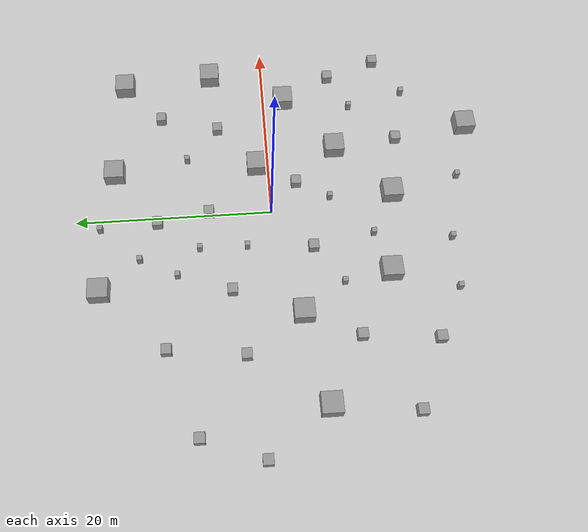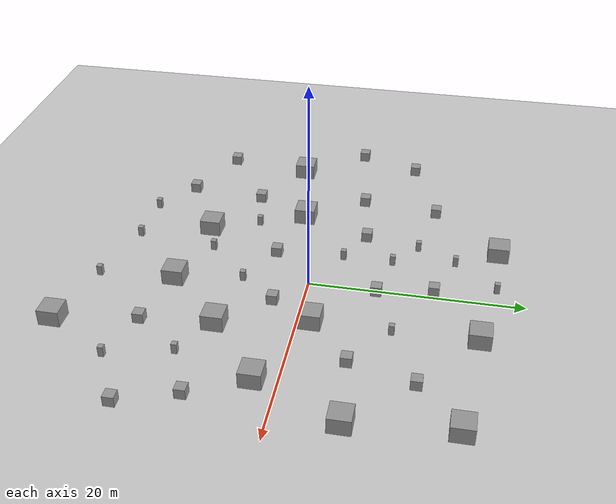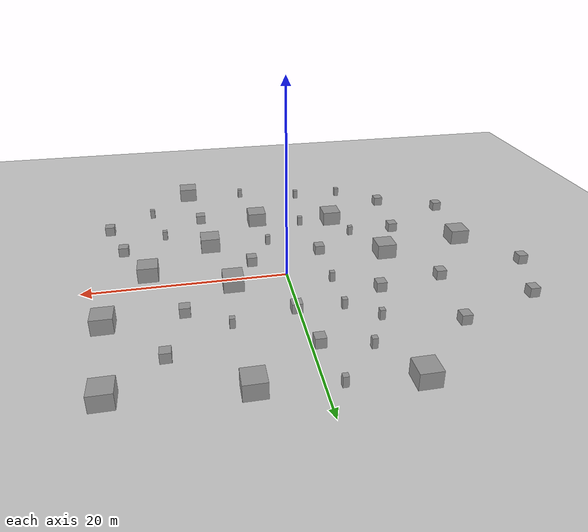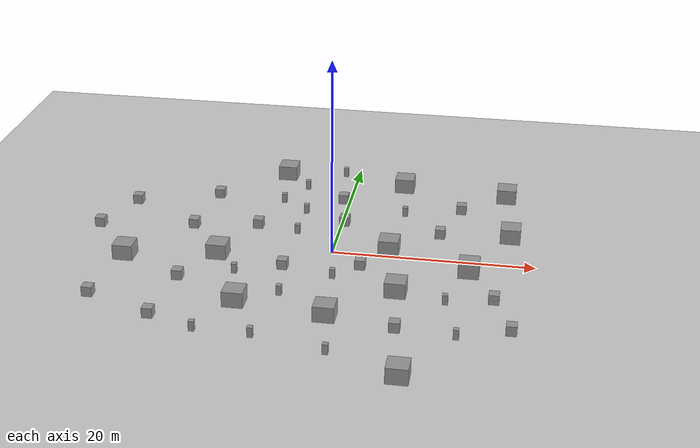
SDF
<sdf version="1.6">
 <world name="default">
  <light name="sun" type="directional">
   <pose>0 0 10 0 -0 0</pose>
   <diffuse>0.8 0.8 0.8 1</diffuse>
   <specular>0.2 0.2 0.2 1</specular>
   <attenuation>
    <range>1000</range>
    <constant>0.9</constant>
    <linear>0.01</linear>
    <quadratic>0.001</quadratic>
   </attenuation>
   <direction>-0.5 0.1 -0.9</direction>
  </light>
  <model name="ground_plane">
   <static>1</static>
   <link name="link">
    <collision name="collision">
     <geometry><plane><normal>0 0 1</normal><size>100 100</size></plane></geometry>
     <surface>
      <contact><collide_bitmask>65535</collide_bitmask></contact>
      <friction><ode><mu>100</mu><mu2>50</mu2></ode></friction>
     </surface>
    </collision>
    <visual name="visual">
     <cast_shadows>0</cast_shadows>
     <geometry><plane><normal>0 0 1</normal><size>100 100</size></plane></geometry>
     <material>
      <script><uri>file://media/materials/scripts/gazebo.material</uri><name>Gazebo/Grey</name></script>
     </material>
    </visual>
   </link>
  </model>
  <gravity>0 0 -9.8</gravity>
  <magnetic_field>6e-06 2.3e-05 -4.2e-05</magnetic_field>
  <atmosphere type="adiabatic"/>
  <physics name="default_physics" default="0" type="ode">
   <max_step_size>0.001</max_step_size>
   <real_time_factor>1</real_time_factor>
   <real_time_update_rate>1000</real_time_update_rate>
  </physics>
  <scene><ambient>0.4 0.4 0.4 1</ambient><background>0.7 0.7 0.7 1</background><shadows>1</shadows></scene>
  <audio><device>default</device></audio>
  <spherical_coordinates>
   <surface_model>EARTH_WGS84</surface_model>
   <latitude_deg>0</latitude_deg>
   <longitude_deg>0</longitude_deg>
   <elevation>0</elevation>
   <heading_deg>0</heading_deg>
  </spherical_coordinates>
  <model name="unit_box">
   <pose>-4.20212 -3.90314 0.5 0 -0 0</pose>
   <link name="link">
    <inertial>
     <mass>1</mass>
     <inertia>
      <ixx>0.166667</ixx>
      <ixy>0</ixy>
      <ixz>0</ixz>
      <iyy>0.166667</iyy>
      <iyz>0</iyz>
      <izz>0.166667</izz>
     </inertia>
    </inertial>
    <collision name="collision"><geometry><box><size>1 1 1</size></box></geometry></collision>
    <visual name="visual">
     <geometry><box><size>1 1 1</size></box></geometry>
     <material>
      <script><name>Gazebo/Grey</name><uri>file://media/materials/scripts/gazebo.material</uri></script>
     </material>
    </visual>
   </link>
  </model>
  <model name="unit_box_0">
   <pose>-8.36923 4.37364 0.5 -0 -0 -0</pose>
   <link name="link">
    <inertial>
     <mass>1</mass>
     <inertia>
      <ixx>0.166667</ixx>
      <ixy>0</ixy>
      <ixz>0</ixz>
      <iyy>0.166667</iyy>
      <iyz>0</iyz>
      <izz>0.166667</izz>
     </inertia>
    </inertial>
    <collision name="collision"><geometry><box><size>1 1 1</size></box></geometry></collision>
    <visual name="visual">
     <geometry><box><size>1 1 1</size></box></geometry>
     <material>
      <script><name>Gazebo/Grey</name><uri>file://media/materials/scripts/gazebo.material</uri></script>
     </material>
    </visual>
   </link>
  </model>
  <model name="unit_box_1">
   <pose>-0.684189 11.6081 0.5 0 -0 0</pose>
   <link name="link">
    <inertial>
     <mass>1</mass>
     <inertia>
      <ixx>0.166667</ixx>
      <ixy>0</ixy>
      <ixz>0</ixz>
      <iyy>0.166667</iyy>
      <iyz>0</iyz>
      <izz>0.166667</izz>
     </inertia>
    </inertial>
    <collision name="collision"><geometry><box><size>1 1 1</size></box></geometry></collision>
    <visual name="visual">
     <geometry><box><size>1 1 1</size></box></geometry>
     <material>
      <script><name>Gazebo/Grey</name><uri>file://media/materials/scripts/gazebo.material</uri></script>
     </material>
    </visual>
   </link>
  </model>
  <model name="0.5x0.5_cube_4">
   <link name="link">
    <inertial>
     <mass>1</mass>
     <inertia>
      <ixx>0.166667</ixx>
      <ixy>0</ixy>
      <ixz>0</ixz>
      <iyy>0.166667</iyy>
      <iyz>0</iyz>
      <izz>0.166667</izz>
     </inertia>
    </inertial>
    <visual name="visual">
     <geometry><box><size>0.5 0.5 1</size></box></geometry>
     <material>
      <script><name>Gazebo/Grey</name><uri>file://media/materials/scripts/gazebo.material</uri></script>
      <shader type="vertex"><normal_map>__default__</normal_map></shader>
      <ambient>0.3 0.3 0.3 1</ambient>
      <diffuse>0.7 0.7 0.7 1</diffuse>
      <specular>0.01 0.01 0.01 1</specular>
      <emissive>0 0 0 1</emissive>
     </material>
     <pose>0 0 0.5 0 -0 0</pose>
    </visual>
    <collision name="collision">
     <geometry><box><size>1 1 1</size></box></geometry>
     <surface>
      <friction>
       <ode><mu>1</mu><mu2>1</mu2><fdir1>0 0 0</fdir1><slip1>0</slip1><slip2>0</slip2></ode>
       <torsional>
        <coefficient>1</coefficient>
        <patch_radius>0</patch_radius>
        <surface_radius>0</surface_radius>
        <use_patch_radius>1</use_patch_radius>
        <ode><slip>0</slip></ode>
       </torsional>
      </friction>
      <bounce><restitution_coefficient>0</restitution_coefficient><threshold>1e+06</threshold></bounce>
      <contact>
       <collide_without_contact>0</collide_without_contact>
       <collide_without_contact_bitmask>1</collide_without_contact_bitmask>
       <collide_bitmask>1</collide_bitmask>
       <ode>
        <soft_cfm>0</soft_cfm>
        <soft_erp>0.2</soft_erp>
        <kp>1e+13</kp>
        <kd>1</kd>
        <max_vel>0.01</max_vel>
        <min_depth>0</min_depth>
       </ode>
       <bullet>
        <split_impulse>1</split_impulse>
        <split_impulse_penetration_threshold>-0.01</split_impulse_penetration_threshold>
        <soft_cfm>0</soft_cfm>
        <soft_erp>0.2</soft_erp>
        <kp>1e+13</kp>
        <kd>1</kd>
       </bullet>
      </contact>
     </surface>
    </collision>
   </link>
   <static>0</static>
   <pose>1.04625 -6.00454 0.5 0 -0 0</pose>
  </model>
  <model name="2x2_cube">
   <link name="link">
    <inertial>
     <mass>1</mass>
     <inertia>
      <ixx>0.166667</ixx>
      <ixy>0</ixy>
      <ixz>0</ixz>
      <iyy>0.166667</iyy>
      <iyz>0</iyz>
      <izz>0.166667</izz>
     </inertia>
    </inertial>
    <visual name="visual">
     <geometry><box><size>2 2 2</size></box></geometry>
     <material>
      <script><name>Gazebo/Grey</name><uri>file://media/materials/scripts/gazebo.material</uri></script>
      <shader type="vertex"><normal_map>__default__</normal_map></shader>
      <ambient>0.3 0.3 0.3 1</ambient>
      <diffuse>0.7 0.7 0.7 1</diffuse>
      <specular>0.01 0.01 0.01 1</specular>
      <emissive>0 0 0 1</emissive>
     </material>
    </visual>
    <collision name="collision">
     <geometry><box><size>1 1 1</size></box></geometry>
     <surface>
      <friction>
       <ode><mu>1</mu><mu2>1</mu2><fdir1>0 0 0</fdir1><slip1>0</slip1><slip2>0</slip2></ode>
       <torsional>
        <coefficient>1</coefficient>
        <patch_radius>0</patch_radius>
        <surface_radius>0</surface_radius>
        <use_patch_radius>1</use_patch_radius>
        <ode><slip>0</slip></ode>
       </torsional>
      </friction>
      <bounce><restitution_coefficient>0</restitution_coefficient><threshold>1e+06</threshold></bounce>
      <contact>
       <collide_without_contact>0</collide_without_contact>
       <collide_without_contact_bitmask>1</collide_without_contact_bitmask>
       <collide_bitmask>1</collide_bitmask>
       <ode>
        <soft_cfm>0</soft_cfm>
        <soft_erp>0.2</soft_erp>
        <kp>1e+13</kp>
        <kd>1</kd>
        <max_vel>0.01</max_vel>
        <min_depth>0</min_depth>
       </ode>
       <bullet>
        <split_impulse>1</split_impulse>
        <split_impulse_penetration_threshold>-0.01</split_impulse_penetration_threshold>
        <soft_cfm>0</soft_cfm>
        <soft_erp>0.2</soft_erp>
        <kp>1e+13</kp>
        <kd>1</kd>
       </bullet>
      </contact>
     </surface>
    </collision>
   </link>
   <static>0</static>
   <pose>5.52974 1.21304 0.5 0 -0 0</pose>
  </model>
  <model name="unit_box_2">
   <pose>0.255872 6.3816 0.5 -0 -0 -0</pose>
   <link name="link">
    <inertial>
     <mass>1</mass>
     <inertia>
      <ixx>0.166667</ixx>
      <ixy>0</ixy>
      <ixz>0</ixz>
      <iyy>0.166667</iyy>
      <iyz>0</iyz>
      <izz>0.166667</izz>
     </inertia>
    </inertial>
    <collision name="collision"><geometry><box><size>1 1 1</size></box></geometry></collision>
    <visual name="visual">
     <geometry><box><size>1 1 1</size></box></geometry>
     <material>
      <script><name>Gazebo/Grey</name><uri>file://media/materials/scripts/gazebo.material</uri></script>
     </material>
    </visual>
   </link>
  </model>
  <model name="0.5x0.5_cube_4_0">
   <link name="link">
    <inertial>
     <mass>1</mass>
     <inertia>
      <ixx>0.166667</ixx>
      <ixy>0</ixy>
      <ixz>0</ixz>
      <iyy>0.166667</iyy>
      <iyz>0</iyz>
      <izz>0.166667</izz>
     </inertia>
    </inertial>
    <visual name="visual">
     <geometry><box><size>0.5 0.5 1</size></box></geometry>
     <material>
      <script><name>Gazebo/Grey</name><uri>file://media/materials/scripts/gazebo.material</uri></script>
      <shader type="vertex"><normal_map>__default__</normal_map></shader>
      <ambient>0.3 0.3 0.3 1</ambient>
      <diffuse>0.7 0.7 0.7 1</diffuse>
      <specular>0.01 0.01 0.01 1</specular>
      <emissive>0 0 0 1</emissive>
     </material>
     <pose>0 0 0.5 0 -0 0</pose>
    </visual>
    <collision name="collision">
     <geometry><box><size>1 1 1</size></box></geometry>
     <surface>
      <friction>
       <ode><mu>1</mu><mu2>1</mu2><fdir1>0 0 0</fdir1><slip1>0</slip1><slip2>0</slip2></ode>
       <torsional>
        <coefficient>1</coefficient>
        <patch_radius>0</patch_radius>
        <surface_radius>0</surface_radius>
        <use_patch_radius>1</use_patch_radius>
        <ode><slip>0</slip></ode>
       </torsional>
      </friction>
      <bounce><restitution_coefficient>0</restitution_coefficient><threshold>1e+06</threshold></bounce>
      <contact>
       <collide_without_contact>0</collide_without_contact>
       <collide_without_contact_bitmask>1</collide_without_contact_bitmask>
       <collide_bitmask>1</collide_bitmask>
       <ode>
        <soft_cfm>0</soft_cfm>
        <soft_erp>0.2</soft_erp>
        <kp>1e+13</kp>
        <kd>1</kd>
        <max_vel>0.01</max_vel>
        <min_depth>0</min_depth>
       </ode>
       <bullet>
        <split_impulse>1</split_impulse>
        <split_impulse_penetration_threshold>-0.01</split_impulse_penetration_threshold>
        <soft_cfm>0</soft_cfm>
        <soft_erp>0.2</soft_erp>
        <kp>1e+13</kp>
        <kd>1</kd>
       </bullet>
      </contact>
     </surface>
    </collision>
   </link>
   <static>0</static>
   <pose>-3.97694 2.68308 0.5 0 -0 0</pose>
  </model>
  <model name="2x2_cube_0">
   <link name="link">
    <inertial>
     <mass>1</mass>
     <inertia>
      <ixx>0.166667</ixx>
      <ixy>0</ixy>
      <ixz>0</ixz>
      <iyy>0.166667</iyy>
      <iyz>0</iyz>
      <izz>0.166667</izz>
     </inertia>
    </inertial>
    <visual name="visual">
     <geometry><box><size>2 2 2</size></box></geometry>
     <material>
      <script><name>Gazebo/Grey</name><uri>file://media/materials/scripts/gazebo.material</uri></script>
      <shader type="vertex"><normal_map>__default__</normal_map></shader>
      <ambient>0.3 0.3 0.3 1</ambient>
      <diffuse>0.7 0.7 0.7 1</diffuse>
      <specular>0.01 0.01 0.01 1</specular>
      <emissive>0 0 0 1</emissive>
     </material>
    </visual>
    <collision name="collision">
     <geometry><box><size>1 1 1</size></box></geometry>
     <surface>
      <friction>
       <ode><mu>1</mu><mu2>1</mu2><fdir1>0 0 0</fdir1><slip1>0</slip1><slip2>0</slip2></ode>
       <torsional>
        <coefficient>1</coefficient>
        <patch_radius>0</patch_radius>
        <surface_radius>0</surface_radius>
        <use_patch_radius>1</use_patch_radius>
        <ode><slip>0</slip></ode>
       </torsional>
      </friction>
      <bounce><restitution_coefficient>0</restitution_coefficient><threshold>1e+06</threshold></bounce>
      <contact>
       <collide_without_contact>0</collide_without_contact>
       <collide_without_contact_bitmask>1</collide_without_contact_bitmask>
       <collide_bitmask>1</collide_bitmask>
       <ode>
        <soft_cfm>0</soft_cfm>
        <soft_erp>0.2</soft_erp>
        <kp>1e+13</kp>
        <kd>1</kd>
        <max_vel>0.01</max_vel>
        <min_depth>0</min_depth>
       </ode>
       <bullet>
        <split_impulse>1</split_impulse>
        <split_impulse_penetration_threshold>-0.01</split_impulse_penetration_threshold>
        <soft_cfm>0</soft_cfm>
        <soft_erp>0.2</soft_erp>
        <kp>1e+13</kp>
        <kd>1</kd>
       </bullet>
      </contact>
     </surface>
    </collision>
   </link>
   <static>0</static>
   <pose>-11.0166 -2.32935 0.5 0 -0 0</pose>
  </model>
  <model name="2x2_cube_1">
   <link name="link">
    <inertial>
     <mass>1</mass>
     <inertia>
      <ixx>0.166667</ixx>
      <ixy>0</ixy>
      <ixz>0</ixz>
      <iyy>0.166667</iyy>
      <iyz>0</iyz>
      <izz>0.166667</izz>
     </inertia>
    </inertial>
    <visual name="visual">
     <geometry><box><size>2 2 2</size></box></geometry>
     <material>
      <script><name>Gazebo/Grey</name><uri>file://media/materials/scripts/gazebo.material</uri></script>
      <shader type="vertex"><normal_map>__default__</normal_map></shader>
      <ambient>0.3 0.3 0.3 1</ambient>
      <diffuse>0.7 0.7 0.7 1</diffuse>
      <specular>0.01 0.01 0.01 1</specular>
      <emissive>0 0 0 1</emissive>
     </material>
    </visual>
    <collision name="collision">
     <geometry><box><size>1 1 1</size></box></geometry>
     <surface>
      <friction>
       <ode><mu>1</mu><mu2>1</mu2><fdir1>0 0 0</fdir1><slip1>0</slip1><slip2>0</slip2></ode>
       <torsional>
        <coefficient>1</coefficient>
        <patch_radius>0</patch_radius>
        <surface_radius>0</surface_radius>
        <use_patch_radius>1</use_patch_radius>
        <ode><slip>0</slip></ode>
       </torsional>
      </friction>
      <bounce><restitution_coefficient>0</restitution_coefficient><threshold>1e+06</threshold></bounce>
      <contact>
       <collide_without_contact>0</collide_without_contact>
       <collide_without_contact_bitmask>1</collide_without_contact_bitmask>
       <collide_bitmask>1</collide_bitmask>
       <ode>
        <soft_cfm>0</soft_cfm>
        <soft_erp>0.2</soft_erp>
        <kp>1e+13</kp>
        <kd>1</kd>
        <max_vel>0.01</max_vel>
        <min_depth>0</min_depth>
       </ode>
       <bullet>
        <split_impulse>1</split_impulse>
        <split_impulse_penetration_threshold>-0.01</split_impulse_penetration_threshold>
        <soft_cfm>0</soft_cfm>
        <soft_erp>0.2</soft_erp>
        <kp>1e+13</kp>
        <kd>1</kd>
       </bullet>
      </contact>
     </surface>
    </collision>
   </link>
   <static>0</static>
   <pose>-7.2358 -11.2675 0.5 0 -0 0</pose>
  </model>
  <model name="2x2_cube_2">
   <link name="link">
    <inertial>
     <mass>1</mass>
     <inertia>
      <ixx>0.166667</ixx>
      <ixy>0</ixy>
      <ixz>0</ixz>
      <iyy>0.166667</iyy>
      <iyz>0</iyz>
      <izz>0.166667</izz>
     </inertia>
    </inertial>
    <visual name="visual">
     <geometry><box><size>2 2 2</size></box></geometry>
     <material>
      <script><name>Gazebo/Grey</name><uri>file://media/materials/scripts/gazebo.material</uri></script>
      <shader type="vertex"><normal_map>__default__</normal_map></shader>
      <ambient>0.3 0.3 0.3 1</ambient>
      <diffuse>0.7 0.7 0.7 1</diffuse>
      <specular>0.01 0.01 0.01 1</specular>
      <emissive>0 0 0 1</emissive>
     </material>
    </visual>
    <collision name="collision">
     <geometry><box><size>1 1 1</size></box></geometry>
     <surface>
      <friction>
       <ode><mu>1</mu><mu2>1</mu2><fdir1>0 0 0</fdir1><slip1>0</slip1><slip2>0</slip2></ode>
       <torsional>
        <coefficient>1</coefficient>
        <patch_radius>0</patch_radius>
        <surface_radius>0</surface_radius>
        <use_patch_radius>1</use_patch_radius>
        <ode><slip>0</slip></ode>
       </torsional>
      </friction>
      <bounce><restitution_coefficient>0</restitution_coefficient><threshold>1e+06</threshold></bounce>
      <contact>
       <collide_without_contact>0</collide_without_contact>
       <collide_without_contact_bitmask>1</collide_without_contact_bitmask>
       <collide_bitmask>1</collide_bitmask>
       <ode>
        <soft_cfm>0</soft_cfm>
        <soft_erp>0.2</soft_erp>
        <kp>1e+13</kp>
        <kd>1</kd>
        <max_vel>0.01</max_vel>
        <min_depth>0</min_depth>
       </ode>
       <bullet>
        <split_impulse>1</split_impulse>
        <split_impulse_penetration_threshold>-0.01</split_impulse_penetration_threshold>
        <soft_cfm>0</soft_cfm>
        <soft_erp>0.2</soft_erp>
        <kp>1e+13</kp>
        <kd>1</kd>
       </bullet>
      </contact>
     </surface>
    </collision>
   </link>
   <static>0</static>
   <pose>1.45527 -12.5043 0.5 0 -0 0</pose>
  </model>
  <model name="2x2_cube_3">
   <link name="link">
    <inertial>
     <mass>1</mass>
     <inertia>
      <ixx>0.166667</ixx>
      <ixy>0</ixy>
      <ixz>0</ixz>
      <iyy>0.166667</iyy>
      <iyz>0</iyz>
      <izz>0.166667</izz>
     </inertia>
    </inertial>
    <visual name="visual">
     <geometry><box><size>2 2 2</size></box></geometry>
     <material>
      <script><name>Gazebo/Grey</name><uri>file://media/materials/scripts/gazebo.material</uri></script>
      <shader type="vertex"><normal_map>__default__</normal_map></shader>
      <ambient>0.3 0.3 0.3 1</ambient>
      <diffuse>0.7 0.7 0.7 1</diffuse>
      <specular>0.01 0.01 0.01 1</specular>
      <emissive>0 0 0 1</emissive>
     </material>
    </visual>
    <collision name="collision">
     <geometry><box><size>1 1 1</size></box></geometry>
     <surface>
      <friction>
       <ode><mu>1</mu><mu2>1</mu2><fdir1>0 0 0</fdir1><slip1>0</slip1><slip2>0</slip2></ode>
       <torsional>
        <coefficient>1</coefficient>
        <patch_radius>0</patch_radius>
        <surface_radius>0</surface_radius>
        <use_patch_radius>1</use_patch_radius>
        <ode><slip>0</slip></ode>
       </torsional>
      </friction>
      <bounce><restitution_coefficient>0</restitution_coefficient><threshold>1e+06</threshold></bounce>
      <contact>
       <collide_without_contact>0</collide_without_contact>
       <collide_without_contact_bitmask>1</collide_without_contact_bitmask>
       <collide_bitmask>1</collide_bitmask>
       <ode>
        <soft_cfm>0</soft_cfm>
        <soft_erp>0.2</soft_erp>
        <kp>1e+13</kp>
        <kd>1</kd>
        <max_vel>0.01</max_vel>
        <min_depth>0</min_depth>
       </ode>
       <bullet>
        <split_impulse>1</split_impulse>
        <split_impulse_penetration_threshold>-0.01</split_impulse_penetration_threshold>
        <soft_cfm>0</soft_cfm>
        <soft_erp>0.2</soft_erp>
        <kp>1e+13</kp>
        <kd>1</kd>
       </bullet>
      </contact>
     </surface>
    </collision>
   </link>
   <static>0</static>
   <pose>7.23428 -7.09701 0.5 0 -0 0</pose>
  </model>
  <model name="unit_box_3">
   <pose>7.95816 -13.7737 0.5 -0 -0 -0</pose>
   <link name="link">
    <inertial>
     <mass>1</mass>
     <inertia>
      <ixx>0.166667</ixx>
      <ixy>0</ixy>
      <ixz>0</ixz>
      <iyy>0.166667</iyy>
      <iyz>0</iyz>
      <izz>0.166667</izz>
     </inertia>
    </inertial>
    <collision name="collision"><geometry><box><size>1 1 1</size></box></geometry></collision>
    <visual name="visual">
     <geometry><box><size>1 1 1</size></box></geometry>
     <material>
      <script><name>Gazebo/Grey</name><uri>file://media/materials/scripts/gazebo.material</uri></script>
     </material>
    </visual>
   </link>
  </model>
  <model name="0.5x0.5_cube_4_1">
   <link name="link">
    <inertial>
     <mass>1</mass>
     <inertia>
      <ixx>0.166667</ixx>
      <ixy>0</ixy>
      <ixz>0</ixz>
      <iyy>0.166667</iyy>
      <iyz>0</iyz>
      <izz>0.166667</izz>
     </inertia>
    </inertial>
    <visual name="visual">
     <geometry><box><size>0.5 0.5 1</size></box></geometry>
     <material>
      <script><name>Gazebo/Grey</name><uri>file://media/materials/scripts/gazebo.material</uri></script>
      <shader type="vertex"><normal_map>__default__</normal_map></shader>
      <ambient>0.3 0.3 0.3 1</ambient>
      <diffuse>0.7 0.7 0.7 1</diffuse>
      <specular>0.01 0.01 0.01 1</specular>
      <emissive>0 0 0 1</emissive>
     </material>
     <pose>0 0 0.5 0 -0 0</pose>
    </visual>
    <collision name="collision">
     <geometry><box><size>1 1 1</size></box></geometry>
     <surface>
      <friction>
       <ode><mu>1</mu><mu2>1</mu2><fdir1>0 0 0</fdir1><slip1>0</slip1><slip2>0</slip2></ode>
       <torsional>
        <coefficient>1</coefficient>
        <patch_radius>0</patch_radius>
        <surface_radius>0</surface_radius>
        <use_patch_radius>1</use_patch_radius>
        <ode><slip>0</slip></ode>
       </torsional>
      </friction>
      <bounce><restitution_coefficient>0</restitution_coefficient><threshold>1e+06</threshold></bounce>
      <contact>
       <collide_without_contact>0</collide_without_contact>
       <collide_without_contact_bitmask>1</collide_without_contact_bitmask>
       <collide_bitmask>1</collide_bitmask>
       <ode>
        <soft_cfm>0</soft_cfm>
        <soft_erp>0.2</soft_erp>
        <kp>1e+13</kp>
        <kd>1</kd>
        <max_vel>0.01</max_vel>
        <min_depth>0</min_depth>
       </ode>
       <bullet>
        <split_impulse>1</split_impulse>
        <split_impulse_penetration_threshold>-0.01</split_impulse_penetration_threshold>
        <soft_cfm>0</soft_cfm>
        <soft_erp>0.2</soft_erp>
        <kp>1e+13</kp>
        <kd>1</kd>
       </bullet>
      </contact>
     </surface>
    </collision>
   </link>
   <static>0</static>
   <pose>-4.25791 -17.7398 0.5 0 -0 0</pose>
  </model>
  <model name="0.5x0.5_cube_4_2">
   <link name="link">
    <inertial>
     <mass>1</mass>
     <inertia>
      <ixx>0.166667</ixx>
      <ixy>0</ixy>
      <ixz>0</ixz>
      <iyy>0.166667</iyy>
      <iyz>0</iyz>
      <izz>0.166667</izz>
     </inertia>
    </inertial>
    <visual name="visual">
     <geometry><box><size>0.5 0.5 1</size></box></geometry>
     <material>
      <script><name>Gazebo/Grey</name><uri>file://media/materials/scripts/gazebo.material</uri></script>
      <shader type="vertex"><normal_map>__default__</normal_map></shader>
      <ambient>0.3 0.3 0.3 1</ambient>
      <diffuse>0.7 0.7 0.7 1</diffuse>
      <specular>0.01 0.01 0.01 1</specular>
      <emissive>0 0 0 1</emissive>
     </material>
     <pose>0 0 0.5 0 -0 0</pose>
    </visual>
    <collision name="collision">
     <geometry><box><size>1 1 1</size></box></geometry>
     <surface>
      <friction>
       <ode><mu>1</mu><mu2>1</mu2><fdir1>0 0 0</fdir1><slip1>0</slip1><slip2>0</slip2></ode>
       <torsional>
        <coefficient>1</coefficient>
        <patch_radius>0</patch_radius>
        <surface_radius>0</surface_radius>
        <use_patch_radius>1</use_patch_radius>
        <ode><slip>0</slip></ode>
       </torsional>
      </friction>
      <bounce><restitution_coefficient>0</restitution_coefficient><threshold>1e+06</threshold></bounce>
      <contact>
       <collide_without_contact>0</collide_without_contact>
       <collide_without_contact_bitmask>1</collide_without_contact_bitmask>
       <collide_bitmask>1</collide_bitmask>
       <ode>
        <soft_cfm>0</soft_cfm>
        <soft_erp>0.2</soft_erp>
        <kp>1e+13</kp>
        <kd>1</kd>
        <max_vel>0.01</max_vel>
        <min_depth>0</min_depth>
       </ode>
       <bullet>
        <split_impulse>1</split_impulse>
        <split_impulse_penetration_threshold>-0.01</split_impulse_penetration_threshold>
        <soft_cfm>0</soft_cfm>
        <soft_erp>0.2</soft_erp>
        <kp>1e+13</kp>
        <kd>1</kd>
       </bullet>
      </contact>
     </surface>
    </collision>
   </link>
   <static>0</static>
   <pose>-3.2947 -9.98565 0.5 0 -0 0</pose>
  </model>
  <model name="0.5x0.5_cube_4_3">
   <link name="link">
    <inertial>
     <mass>1</mass>
     <inertia>
      <ixx>0.166667</ixx>
      <ixy>0</ixy>
      <ixz>0</ixz>
      <iyy>0.166667</iyy>
      <iyz>0</iyz>
      <izz>0.166667</izz>
     </inertia>
    </inertial>
    <visual name="visual">
     <geometry><box><size>0.5 0.5 1</size></box></geometry>
     <material>
      <script><name>Gazebo/Grey</name><uri>file://media/materials/scripts/gazebo.material</uri></script>
      <shader type="vertex"><normal_map>__default__</normal_map></shader>
      <ambient>0.3 0.3 0.3 1</ambient>
      <diffuse>0.7 0.7 0.7 1</diffuse>
      <specular>0.01 0.01 0.01 1</specular>
      <emissive>0 0 0 1</emissive>
     </material>
     <pose>0 0 0.5 0 -0 0</pose>
    </visual>
    <collision name="collision">
     <geometry><box><size>1 1 1</size></box></geometry>
     <surface>
      <friction>
       <ode><mu>1</mu><mu2>1</mu2><fdir1>0 0 0</fdir1><slip1>0</slip1><slip2>0</slip2></ode>
       <torsional>
        <coefficient>1</coefficient>
        <patch_radius>0</patch_radius>
        <surface_radius>0</surface_radius>
        <use_patch_radius>1</use_patch_radius>
        <ode><slip>0</slip></ode>
       </torsional>
      </friction>
      <bounce><restitution_coefficient>0</restitution_coefficient><threshold>1e+06</threshold></bounce>
      <contact>
       <collide_without_contact>0</collide_without_contact>
       <collide_without_contact_bitmask>1</collide_without_contact_bitmask>
       <collide_bitmask>1</collide_bitmask>
       <ode>
        <soft_cfm>0</soft_cfm>
        <soft_erp>0.2</soft_erp>
        <kp>1e+13</kp>
        <kd>1</kd>
        <max_vel>0.01</max_vel>
        <min_depth>0</min_depth>
       </ode>
       <bullet>
        <split_impulse>1</split_impulse>
        <split_impulse_penetration_threshold>-0.01</split_impulse_penetration_threshold>
        <soft_cfm>0</soft_cfm>
        <soft_erp>0.2</soft_erp>
        <kp>1e+13</kp>
        <kd>1</kd>
       </bullet>
      </contact>
     </surface>
    </collision>
   </link>
   <static>0</static>
   <pose>-8.35221 -6.53735 0.5 0 -0 0</pose>
  </model>
  <model name="0.5x0.5_cube_4_4">
   <link name="link">
    <inertial>
     <mass>1</mass>
     <inertia>
      <ixx>0.166667</ixx>
      <ixy>0</ixy>
      <ixz>0</ixz>
      <iyy>0.166667</iyy>
      <iyz>0</iyz>
      <izz>0.166667</izz>
     </inertia>
    </inertial>
    <visual name="visual">
     <geometry><box><size>0.5 0.5 1</size></box></geometry>
     <material>
      <script><name>Gazebo/Grey</name><uri>file://media/materials/scripts/gazebo.material</uri></script>
      <shader type="vertex"><normal_map>__default__</normal_map></shader>
      <ambient>0.3 0.3 0.3 1</ambient>
      <diffuse>0.7 0.7 0.7 1</diffuse>
      <specular>0.01 0.01 0.01 1</specular>
      <emissive>0 0 0 1</emissive>
     </material>
     <pose>0 0 0.5 0 -0 0</pose>
    </visual>
    <collision name="collision">
     <geometry><box><size>1 1 1</size></box></geometry>
     <surface>
      <friction>
       <ode><mu>1</mu><mu2>1</mu2><fdir1>0 0 0</fdir1><slip1>0</slip1><slip2>0</slip2></ode>
       <torsional>
        <coefficient>1</coefficient>
        <patch_radius>0</patch_radius>
        <surface_radius>0</surface_radius>
        <use_patch_radius>1</use_patch_radius>
        <ode><slip>0</slip></ode>
       </torsional>
      </friction>
      <bounce><restitution_coefficient>0</restitution_coefficient><threshold>1e+06</threshold></bounce>
      <contact>
       <collide_without_contact>0</collide_without_contact>
       <collide_without_contact_bitmask>1</collide_without_contact_bitmask>
       <collide_bitmask>1</collide_bitmask>
       <ode>
        <soft_cfm>0</soft_cfm>
        <soft_erp>0.2</soft_erp>
        <kp>1e+13</kp>
        <kd>1</kd>
        <max_vel>0.01</max_vel>
        <min_depth>0</min_depth>
       </ode>
       <bullet>
        <split_impulse>1</split_impulse>
        <split_impulse_penetration_threshold>-0.01</split_impulse_penetration_threshold>
        <soft_cfm>0</soft_cfm>
        <soft_erp>0.2</soft_erp>
        <kp>1e+13</kp>
        <kd>1</kd>
       </bullet>
      </contact>
     </surface>
    </collision>
   </link>
   <static>0</static>
   <pose>-6.72183 9.63011 0.5 0 -0 0</pose>
  </model>
  <model name="0.5x0.5_cube_4_5">
   <link name="link">
    <inertial>
     <mass>1</mass>
     <inertia>
      <ixx>0.166667</ixx>
      <ixy>0</ixy>
      <ixz>0</ixz>
      <iyy>0.166667</iyy>
      <iyz>0</iyz>
      <izz>0.166667</izz>
     </inertia>
    </inertial>
    <visual name="visual">
     <geometry><box><size>0.5 0.5 1</size></box></geometry>
     <material>
      <script><name>Gazebo/Grey</name><uri>file://media/materials/scripts/gazebo.material</uri></script>
      <shader type="vertex"><normal_map>__default__</normal_map></shader>
      <ambient>0.3 0.3 0.3 1</ambient>
      <diffuse>0.7 0.7 0.7 1</diffuse>
      <specular>0.01 0.01 0.01 1</specular>
      <emissive>0 0 0 1</emissive>
     </material>
     <pose>0 0 0.5 0 -0 0</pose>
    </visual>
    <collision name="collision">
     <geometry><box><size>1 1 1</size></box></geometry>
     <surface>
      <friction>
       <ode><mu>1</mu><mu2>1</mu2><fdir1>0 0 0</fdir1><slip1>0</slip1><slip2>0</slip2></ode>
       <torsional>
        <coefficient>1</coefficient>
        <patch_radius>0</patch_radius>
        <surface_radius>0</surface_radius>
        <use_patch_radius>1</use_patch_radius>
        <ode><slip>0</slip></ode>
       </torsional>
      </friction>
      <bounce><restitution_coefficient>0</restitution_coefficient><threshold>1e+06</threshold></bounce>
      <contact>
       <collide_without_contact>0</collide_without_contact>
       <collide_without_contact_bitmask>1</collide_without_contact_bitmask>
       <collide_bitmask>1</collide_bitmask>
       <ode>
        <soft_cfm>0</soft_cfm>
        <soft_erp>0.2</soft_erp>
        <kp>1e+13</kp>
        <kd>1</kd>
        <max_vel>0.01</max_vel>
        <min_depth>0</min_depth>
       </ode>
       <bullet>
        <split_impulse>1</split_impulse>
        <split_impulse_penetration_threshold>-0.01</split_impulse_penetration_threshold>
        <soft_cfm>0</soft_cfm>
        <soft_erp>0.2</soft_erp>
        <kp>1e+13</kp>
        <kd>1</kd>
       </bullet>
      </contact>
     </surface>
    </collision>
   </link>
   <static>0</static>
   <pose>6.26282 8.43975 0.5 0 -0 0</pose>
  </model>
  <model name="unit_box_4">
   <pose>3.22331 -2.73267 0.5 -0 -0 -0</pose>
   <link name="link">
    <inertial>
     <mass>1</mass>
     <inertia>
      <ixx>0.166667</ixx>
      <ixy>0</ixy>
      <ixz>0</ixz>
      <iyy>0.166667</iyy>
      <iyz>0</iyz>
      <izz>0.166667</izz>
     </inertia>
    </inertial>
    <collision name="collision"><geometry><box><size>1 1 1</size></box></geometry></collision>
    <visual name="visual">
     <geometry><box><size>1 1 1</size></box></geometry>
     <material>
      <script><name>Gazebo/Grey</name><uri>file://media/materials/scripts/gazebo.material</uri></script>
     </material>
    </visual>
   </link>
  </model>
  <model name="2x2_cube_4">
   <link name="link">
    <inertial>
     <mass>1</mass>
     <inertia>
      <ixx>0.166667</ixx>
      <ixy>0</ixy>
      <ixz>0</ixz>
      <iyy>0.166667</iyy>
      <iyz>0</iyz>
      <izz>0.166667</izz>
     </inertia>
    </inertial>
    <visual name="visual">
     <geometry><box><size>2 2 2</size></box></geometry>
     <material>
      <script><name>Gazebo/Grey</name><uri>file://media/materials/scripts/gazebo.material</uri></script>
      <shader type="vertex"><normal_map>__default__</normal_map></shader>
      <ambient>0.3 0.3 0.3 1</ambient>
      <diffuse>0.7 0.7 0.7 1</diffuse>
      <specular>0.01 0.01 0.01 1</specular>
      <emissive>0 0 0 1</emissive>
     </material>
    </visual>
    <collision name="collision">
     <geometry><box><size>1 1 1</size></box></geometry>
     <surface>
      <friction>
       <ode><mu>1</mu><mu2>1</mu2><fdir1>0 0 0</fdir1><slip1>0</slip1><slip2>0</slip2></ode>
       <torsional>
        <coefficient>1</coefficient>
        <patch_radius>0</patch_radius>
        <surface_radius>0</surface_radius>
        <use_patch_radius>1</use_patch_radius>
        <ode><slip>0</slip></ode>
       </torsional>
      </friction>
      <bounce><restitution_coefficient>0</restitution_coefficient><threshold>1e+06</threshold></bounce>
      <contact>
       <collide_without_contact>0</collide_without_contact>
       <collide_without_contact_bitmask>1</collide_without_contact_bitmask>
       <collide_bitmask>1</collide_bitmask>
       <ode>
        <soft_cfm>0</soft_cfm>
        <soft_erp>0.2</soft_erp>
        <kp>1e+13</kp>
        <kd>1</kd>
        <max_vel>0.01</max_vel>
        <min_depth>0</min_depth>
       </ode>
       <bullet>
        <split_impulse>1</split_impulse>
        <split_impulse_penetration_threshold>-0.01</split_impulse_penetration_threshold>
        <soft_cfm>0</soft_cfm>
        <soft_erp>0.2</soft_erp>
        <kp>1e+13</kp>
        <kd>1</kd>
       </bullet>
      </contact>
     </surface>
    </collision>
   </link>
   <static>0</static>
   <pose>5.37789 16.0238 0.5 0 -0 0</pose>
  </model>
  <model name="2x2_cube_5">
   <link name="link">
    <inertial>
     <mass>1</mass>
     <inertia>
      <ixx>0.166667</ixx>
      <ixy>0</ixy>
      <ixz>0</ixz>
      <iyy>0.166667</iyy>
      <iyz>0</iyz>
      <izz>0.166667</izz>
     </inertia>
    </inertial>
    <visual name="visual">
     <geometry><box><size>2 2 2</size></box></geometry>
     <material>
      <script><name>Gazebo/Grey</name><uri>file://media/materials/scripts/gazebo.material</uri></script>
      <shader type="vertex"><normal_map>__default__</normal_map></shader>
      <ambient>0.3 0.3 0.3 1</ambient>
      <diffuse>0.7 0.7 0.7 1</diffuse>
      <specular>0.01 0.01 0.01 1</specular>
      <emissive>0 0 0 1</emissive>
     </material>
    </visual>
    <collision name="collision">
     <geometry><box><size>1 1 1</size></box></geometry>
     <surface>
      <friction>
       <ode><mu>1</mu><mu2>1</mu2><fdir1>0 0 0</fdir1><slip1>0</slip1><slip2>0</slip2></ode>
       <torsional>
        <coefficient>1</coefficient>
        <patch_radius>0</patch_radius>
        <surface_radius>0</surface_radius>
        <use_patch_radius>1</use_patch_radius>
        <ode><slip>0</slip></ode>
       </torsional>
      </friction>
      <bounce><restitution_coefficient>0</restitution_coefficient><threshold>1e+06</threshold></bounce>
      <contact>
       <collide_without_contact>0</collide_without_contact>
       <collide_without_contact_bitmask>1</collide_without_contact_bitmask>
       <collide_bitmask>1</collide_bitmask>
       <ode>
        <soft_cfm>0</soft_cfm>
        <soft_erp>0.2</soft_erp>
        <kp>1e+13</kp>
        <kd>1</kd>
        <max_vel>0.01</max_vel>
        <min_depth>0</min_depth>
       </ode>
       <bullet>
        <split_impulse>1</split_impulse>
        <split_impulse_penetration_threshold>-0.01</split_impulse_penetration_threshold>
        <soft_cfm>0</soft_cfm>
        <soft_erp>0.2</soft_erp>
        <kp>1e+13</kp>
        <kd>1</kd>
       </bullet>
      </contact>
     </surface>
    </collision>
   </link>
   <static>0</static>
   <pose>-7.73173 17.3042 0.5 0 -0 0</pose>
  </model>
  <model name="unit_box_5">
   <pose>-13.6613 -7.61768 0.5 0 -0 0</pose>
   <link name="link">
    <inertial>
     <mass>1</mass>
     <inertia>
      <ixx>0.166667</ixx>
      <ixy>0</ixy>
      <ixz>0</ixz>
      <iyy>0.166667</iyy>
      <iyz>0</iyz>
      <izz>0.166667</izz>
     </inertia>
    </inertial>
    <collision name="collision"><geometry><box><size>1 1 1</size></box></geometry></collision>
    <visual name="visual">
     <geometry><box><size>1 1 1</size></box></geometry>
     <material>
      <script><name>Gazebo/Grey</name><uri>file://media/materials/scripts/gazebo.material</uri></script>
     </material>
    </visual>
   </link>
  </model>
  <model name="unit_box_6">
   <pose>-14.8999 3.34623 0.5 -0 -0 -0</pose>
   <link name="link">
    <inertial>
     <mass>1</mass>
     <inertia>
      <ixx>0.166667</ixx>
      <ixy>0</ixy>
      <ixz>0</ixz>
      <iyy>0.166667</iyy>
      <iyz>0</iyz>
      <izz>0.166667</izz>
     </inertia>
    </inertial>
    <collision name="collision"><geometry><box><size>1 1 1</size></box></geometry></collision>
    <visual name="visual">
     <geometry><box><size>1 1 1</size></box></geometry>
     <material>
      <script><name>Gazebo/Grey</name><uri>file://media/materials/scripts/gazebo.material</uri></script>
     </material>
    </visual>
   </link>
  </model>
  <model name="unit_box_7">
   <pose>-14.0039 10.8372 0.5 0 -0 0</pose>
   <link name="link">
    <inertial>
     <mass>1</mass>
     <inertia>
      <ixx>0.166667</ixx>
      <ixy>0</ixy>
      <ixz>0</ixz>
      <iyy>0.166667</iyy>
      <iyz>0</iyz>
      <izz>0.166667</izz>
     </inertia>
    </inertial>
    <collision name="collision"><geometry><box><size>1 1 1</size></box></geometry></collision>
    <visual name="visual">
     <geometry><box><size>1 1 1</size></box></geometry>
     <material>
      <script><name>Gazebo/Grey</name><uri>file://media/materials/scripts/gazebo.material</uri></script>
     </material>
    </visual>
   </link>
  </model>
  <model name="unit_box_8">
   <pose>10.2338 5.14923 0.5 -0 -0 -0</pose>
   <link name="link">
    <inertial>
     <mass>1</mass>
     <inertia>
      <ixx>0.166667</ixx>
      <ixy>0</ixy>
      <ixz>0</ixz>
      <iyy>0.166667</iyy>
      <iyz>0</iyz>
      <izz>0.166667</izz>
     </inertia>
    </inertial>
    <collision name="collision"><geometry><box><size>1 1 1</size></box></geometry></collision>
    <visual name="visual">
     <geometry><box><size>1 1 1</size></box></geometry>
     <material>
      <script><name>Gazebo/Grey</name><uri>file://media/materials/scripts/gazebo.material</uri></script>
     </material>
    </visual>
   </link>
  </model>
  <model name="2x2_cube_6">
   <link name="link">
    <inertial>
     <mass>1</mass>
     <inertia>
      <ixx>0.166667</ixx>
      <ixy>0</ixy>
      <ixz>0</ixz>
      <iyy>0.166667</iyy>
      <iyz>0</iyz>
      <izz>0.166667</izz>
     </inertia>
    </inertial>
    <visual name="visual">
     <geometry><box><size>2 2 2</size></box></geometry>
     <material>
      <script><name>Gazebo/Grey</name><uri>file://media/materials/scripts/gazebo.material</uri></script>
      <shader type="vertex"><normal_map>__default__</normal_map></shader>
      <ambient>0.3 0.3 0.3 1</ambient>
      <diffuse>0.7 0.7 0.7 1</diffuse>
      <specular>0.01 0.01 0.01 1</specular>
      <emissive>0 0 0 1</emissive>
     </material>
    </visual>
    <collision name="collision">
     <geometry><box><size>1 1 1</size></box></geometry>
     <surface>
      <friction>
       <ode><mu>1</mu><mu2>1</mu2><fdir1>0 0 0</fdir1><slip1>0</slip1><slip2>0</slip2></ode>
       <torsional>
        <coefficient>1</coefficient>
        <patch_radius>0</patch_radius>
        <surface_radius>0</surface_radius>
        <use_patch_radius>1</use_patch_radius>
        <ode><slip>0</slip></ode>
       </torsional>
      </friction>
      <bounce><restitution_coefficient>0</restitution_coefficient><threshold>1e+06</threshold></bounce>
      <contact>
       <collide_without_contact>0</collide_without_contact>
       <collide_without_contact_bitmask>1</collide_without_contact_bitmask>
       <collide_bitmask>1</collide_bitmask>
       <ode>
        <soft_cfm>0</soft_cfm>
        <soft_erp>0.2</soft_erp>
        <kp>1e+13</kp>
        <kd>1</kd>
        <max_vel>0.01</max_vel>
        <min_depth>0</min_depth>
       </ode>
       <bullet>
        <split_impulse>1</split_impulse>
        <split_impulse_penetration_threshold>-0.01</split_impulse_penetration_threshold>
        <soft_cfm>0</soft_cfm>
        <soft_erp>0.2</soft_erp>
        <kp>1e+13</kp>
        <kd>1</kd>
       </bullet>
      </contact>
     </surface>
    </collision>
   </link>
   <static>0</static>
   <pose>13.6742 -2.13898 0.5 0 -0 0</pose>
  </model>
  <model name="unit_box_9">
   <pose>11.8992 11.1459 0.5 -0 -0 -0</pose>
   <link name="link">
    <inertial>
     <mass>1</mass>
     <inertia>
      <ixx>0.166667</ixx>
      <ixy>0</ixy>
      <ixz>0</ixz>
      <iyy>0.166667</iyy>
      <iyz>0</iyz>
      <izz>0.166667</izz>
     </inertia>
    </inertial>
    <collision name="collision"><geometry><box><size>1 1 1</size></box></geometry></collision>
    <visual name="visual">
     <geometry><box><size>1 1 1</size></box></geometry>
     <material>
      <script><name>Gazebo/Grey</name><uri>file://media/materials/scripts/gazebo.material</uri></script>
     </material>
    </visual>
   </link>
  </model>
  <model name="0.5x0.5_cube_4_6">
   <link name="link">
    <inertial>
     <mass>1</mass>
     <inertia>
      <ixx>0.166667</ixx>
      <ixy>0</ixy>
      <ixz>0</ixz>
      <iyy>0.166667</iyy>
      <iyz>0</iyz>
      <izz>0.166667</izz>
     </inertia>
    </inertial>
    <visual name="visual">
     <geometry><box><size>0.5 0.5 1</size></box></geometry>
     <material>
      <script><name>Gazebo/Grey</name><uri>file://media/materials/scripts/gazebo.material</uri></script>
      <shader type="vertex"><normal_map>__default__</normal_map></shader>
      <ambient>0.3 0.3 0.3 1</ambient>
      <diffuse>0.7 0.7 0.7 1</diffuse>
      <specular>0.01 0.01 0.01 1</specular>
      <emissive>0 0 0 1</emissive>
     </material>
     <pose>0 0 0.5 0 -0 0</pose>
    </visual>
    <collision name="collision">
     <geometry><box><size>1 1 1</size></box></geometry>
     <surface>
      <friction>
       <ode><mu>1</mu><mu2>1</mu2><fdir1>0 0 0</fdir1><slip1>0</slip1><slip2>0</slip2></ode>
       <torsional>
        <coefficient>1</coefficient>
        <patch_radius>0</patch_radius>
        <surface_radius>0</surface_radius>
        <use_patch_radius>1</use_patch_radius>
        <ode><slip>0</slip></ode>
       </torsional>
      </friction>
      <bounce><restitution_coefficient>0</restitution_coefficient><threshold>1e+06</threshold></bounce>
      <contact>
       <collide_without_contact>0</collide_without_contact>
       <collide_without_contact_bitmask>1</collide_without_contact_bitmask>
       <collide_bitmask>1</collide_bitmask>
       <ode>
        <soft_cfm>0</soft_cfm>
        <soft_erp>0.2</soft_erp>
        <kp>1e+13</kp>
        <kd>1</kd>
        <max_vel>0.01</max_vel>
        <min_depth>0</min_depth>
       </ode>
       <bullet>
        <split_impulse>1</split_impulse>
        <split_impulse_penetration_threshold>-0.01</split_impulse_penetration_threshold>
        <soft_cfm>0</soft_cfm>
        <soft_erp>0.2</soft_erp>
        <kp>1e+13</kp>
        <kd>1</kd>
       </bullet>
      </contact>
     </surface>
    </collision>
   </link>
   <static>0</static>
   <pose>12.0178 -9.17388 0.5 0 -0 0</pose>
  </model>
  <model name="unit_box_10">
   <pose>-14.3559 -14.9967 0.5 -0 -0 -0</pose>
   <link name="link">
    <inertial>
     <mass>1</mass>
     <inertia>
      <ixx>0.166667</ixx>
      <ixy>0</ixy>
      <ixz>0</ixz>
      <iyy>0.166667</iyy>
      <iyz>0</iyz>
      <izz>0.166667</izz>
     </inertia>
    </inertial>
    <collision name="collision"><geometry><box><size>1 1 1</size></box></geometry></collision>
    <visual name="visual">
     <geometry><box><size>1 1 1</size></box></geometry>
     <material>
      <script><name>Gazebo/Grey</name><uri>file://media/materials/scripts/gazebo.material</uri></script>
     </material>
    </visual>
   </link>
  </model>
  <model name="0.5x0.5_cube_4_7">
   <link name="link">
    <inertial>
     <mass>1</mass>
     <inertia>
      <ixx>0.166667</ixx>
      <ixy>0</ixy>
      <ixz>0</ixz>
      <iyy>0.166667</iyy>
      <iyz>0</iyz>
      <izz>0.166667</izz>
     </inertia>
    </inertial>
    <visual name="visual">
     <geometry><box><size>0.5 0.5 1</size></box></geometry>
     <material>
      <script><name>Gazebo/Grey</name><uri>file://media/materials/scripts/gazebo.material</uri></script>
      <shader type="vertex"><normal_map>__default__</normal_map></shader>
      <ambient>0.3 0.3 0.3 1</ambient>
      <diffuse>0.7 0.7 0.7 1</diffuse>
      <specular>0.01 0.01 0.01 1</specular>
      <emissive>0 0 0 1</emissive>
     </material>
     <pose>0 0 0.5 0 -0 0</pose>
    </visual>
    <collision name="collision">
     <geometry><box><size>1 1 1</size></box></geometry>
     <surface>
      <friction>
       <ode><mu>1</mu><mu2>1</mu2><fdir1>0 0 0</fdir1><slip1>0</slip1><slip2>0</slip2></ode>
       <torsional>
        <coefficient>1</coefficient>
        <patch_radius>0</patch_radius>
        <surface_radius>0</surface_radius>
        <use_patch_radius>1</use_patch_radius>
        <ode><slip>0</slip></ode>
       </torsional>
      </friction>
      <bounce><restitution_coefficient>0</restitution_coefficient><threshold>1e+06</threshold></bounce>
      <contact>
       <collide_without_contact>0</collide_without_contact>
       <collide_without_contact_bitmask>1</collide_without_contact_bitmask>
       <collide_bitmask>1</collide_bitmask>
       <ode>
        <soft_cfm>0</soft_cfm>
        <soft_erp>0.2</soft_erp>
        <kp>1e+13</kp>
        <kd>1</kd>
        <max_vel>0.01</max_vel>
        <min_depth>0</min_depth>
       </ode>
       <bullet>
        <split_impulse>1</split_impulse>
        <split_impulse_penetration_threshold>-0.01</split_impulse_penetration_threshold>
        <soft_cfm>0</soft_cfm>
        <soft_erp>0.2</soft_erp>
        <kp>1e+13</kp>
        <kd>1</kd>
       </bullet>
      </contact>
     </surface>
    </collision>
   </link>
   <static>0</static>
   <pose>2.69088 -19.3742 0.5 0 -0 0</pose>
  </model>
  <model name="2x2_cube_7">
   <link name="link">
    <inertial>
     <mass>1</mass>
     <inertia>
      <ixx>0.166667</ixx>
      <ixy>0</ixy>
      <ixz>0</ixz>
      <iyy>0.166667</iyy>
      <iyz>0</iyz>
      <izz>0.166667</izz>
     </inertia>
    </inertial>
    <visual name="visual">
     <geometry><box><size>2 2 2</size></box></geometry>
     <material>
      <script><name>Gazebo/Grey</name><uri>file://media/materials/scripts/gazebo.material</uri></script>
      <shader type="vertex"><normal_map>__default__</normal_map></shader>
      <ambient>0.3 0.3 0.3 1</ambient>
      <diffuse>0.7 0.7 0.7 1</diffuse>
      <specular>0.01 0.01 0.01 1</specular>
      <emissive>0 0 0 1</emissive>
     </material>
    </visual>
    <collision name="collision">
     <geometry><box><size>1 1 1</size></box></geometry>
     <surface>
      <friction>
       <ode><mu>1</mu><mu2>1</mu2><fdir1>0 0 0</fdir1><slip1>0</slip1><slip2>0</slip2></ode>
       <torsional>
        <coefficient>1</coefficient>
        <patch_radius>0</patch_radius>
        <surface_radius>0</surface_radius>
        <use_patch_radius>1</use_patch_radius>
        <ode><slip>0</slip></ode>
       </torsional>
      </friction>
      <bounce><restitution_coefficient>0</restitution_coefficient><threshold>1e+06</threshold></bounce>
      <contact>
       <collide_without_contact>0</collide_without_contact>
       <collide_without_contact_bitmask>1</collide_without_contact_bitmask>
       <collide_bitmask>1</collide_bitmask>
       <ode>
        <soft_cfm>0</soft_cfm>
        <soft_erp>0.2</soft_erp>
        <kp>1e+13</kp>
        <kd>1</kd>
        <max_vel>0.01</max_vel>
        <min_depth>0</min_depth>
       </ode>
       <bullet>
        <split_impulse>1</split_impulse>
        <split_impulse_penetration_threshold>-0.01</split_impulse_penetration_threshold>
        <soft_cfm>0</soft_cfm>
        <soft_erp>0.2</soft_erp>
        <kp>1e+13</kp>
        <kd>1</kd>
       </bullet>
      </contact>
     </surface>
    </collision>
   </link>
   <static>0</static>
   <pose>17.2684 5.75436 0.5 0 -0 0</pose>
  </model>
  <model name="2x2_cube_8">
   <link name="link">
    <inertial>
     <mass>1</mass>
     <inertia>
      <ixx>0.166667</ixx>
      <ixy>0</ixy>
      <ixz>0</ixz>
      <iyy>0.166667</iyy>
      <iyz>0</iyz>
      <izz>0.166667</izz>
     </inertia>
    </inertial>
    <visual name="visual">
     <geometry><box><size>2 2 2</size></box></geometry>
     <material>
      <script><name>Gazebo/Grey</name><uri>file://media/materials/scripts/gazebo.material</uri></script>
      <shader type="vertex"><normal_map>__default__</normal_map></shader>
      <ambient>0.3 0.3 0.3 1</ambient>
      <diffuse>0.7 0.7 0.7 1</diffuse>
      <specular>0.01 0.01 0.01 1</specular>
      <emissive>0 0 0 1</emissive>
     </material>
    </visual>
    <collision name="collision">
     <geometry><box><size>1 1 1</size></box></geometry>
     <surface>
      <friction>
       <ode><mu>1</mu><mu2>1</mu2><fdir1>0 0 0</fdir1><slip1>0</slip1><slip2>0</slip2></ode>
       <torsional>
        <coefficient>1</coefficient>
        <patch_radius>0</patch_radius>
        <surface_radius>0</surface_radius>
        <use_patch_radius>1</use_patch_radius>
        <ode><slip>0</slip></ode>
       </torsional>
      </friction>
      <bounce><restitution_coefficient>0</restitution_coefficient><threshold>1e+06</threshold></bounce>
      <contact>
       <collide_without_contact>0</collide_without_contact>
       <collide_without_contact_bitmask>1</collide_without_contact_bitmask>
       <collide_bitmask>1</collide_bitmask>
       <ode>
        <soft_cfm>0</soft_cfm>
        <soft_erp>0.2</soft_erp>
        <kp>1e+13</kp>
        <kd>1</kd>
        <max_vel>0.01</max_vel>
        <min_depth>0</min_depth>
       </ode>
       <bullet>
        <split_impulse>1</split_impulse>
        <split_impulse_penetration_threshold>-0.01</split_impulse_penetration_threshold>
        <soft_cfm>0</soft_cfm>
        <soft_erp>0.2</soft_erp>
        <kp>1e+13</kp>
        <kd>1</kd>
       </bullet>
      </contact>
     </surface>
    </collision>
   </link>
   <static>0</static>
   <pose>-20.0176 -4.00093 0.5 0 -0 0</pose>
  </model>
  <model name="unit_box_11">
   <pose>-21.0147 -12.1472 0.5 -0 -0 -0</pose>
   <link name="link">
    <inertial>
     <mass>1</mass>
     <inertia>
      <ixx>0.166667</ixx>
      <ixy>0</ixy>
      <ixz>0</ixz>
      <iyy>0.166667</iyy>
      <iyz>0</iyz>
      <izz>0.166667</izz>
     </inertia>
    </inertial>
    <collision name="collision"><geometry><box><size>1 1 1</size></box></geometry></collision>
    <visual name="visual">
     <geometry><box><size>1 1 1</size></box></geometry>
     <material>
      <script><name>Gazebo/Grey</name><uri>file://media/materials/scripts/gazebo.material</uri></script>
     </material>
    </visual>
   </link>
  </model>
  <model name="0.5x0.5_cube_4_8">
   <link name="link">
    <inertial>
     <mass>1</mass>
     <inertia>
      <ixx>0.166667</ixx>
      <ixy>0</ixy>
      <ixz>0</ixz>
      <iyy>0.166667</iyy>
      <iyz>0</iyz>
      <izz>0.166667</izz>
     </inertia>
    </inertial>
    <visual name="visual">
     <geometry><box><size>0.5 0.5 1</size></box></geometry>
     <material>
      <script><name>Gazebo/Grey</name><uri>file://media/materials/scripts/gazebo.material</uri></script>
      <shader type="vertex"><normal_map>__default__</normal_map></shader>
      <ambient>0.3 0.3 0.3 1</ambient>
      <diffuse>0.7 0.7 0.7 1</diffuse>
      <specular>0.01 0.01 0.01 1</specular>
      <emissive>0 0 0 1</emissive>
     </material>
     <pose>0 0 0.5 0 -0 0</pose>
    </visual>
    <collision name="collision">
     <geometry><box><size>1 1 1</size></box></geometry>
     <surface>
      <friction>
       <ode><mu>1</mu><mu2>1</mu2><fdir1>0 0 0</fdir1><slip1>0</slip1><slip2>0</slip2></ode>
       <torsional>
        <coefficient>1</coefficient>
        <patch_radius>0</patch_radius>
        <surface_radius>0</surface_radius>
        <use_patch_radius>1</use_patch_radius>
        <ode><slip>0</slip></ode>
       </torsional>
      </friction>
      <bounce><restitution_coefficient>0</restitution_coefficient><threshold>1e+06</threshold></bounce>
      <contact>
       <collide_without_contact>0</collide_without_contact>
       <collide_without_contact_bitmask>1</collide_without_contact_bitmask>
       <collide_bitmask>1</collide_bitmask>
       <ode>
        <soft_cfm>0</soft_cfm>
        <soft_erp>0.2</soft_erp>
        <kp>1e+13</kp>
        <kd>1</kd>
        <max_vel>0.01</max_vel>
        <min_depth>0</min_depth>
       </ode>
       <bullet>
        <split_impulse>1</split_impulse>
        <split_impulse_penetration_threshold>-0.01</split_impulse_penetration_threshold>
        <soft_cfm>0</soft_cfm>
        <soft_erp>0.2</soft_erp>
        <kp>1e+13</kp>
        <kd>1</kd>
       </bullet>
      </contact>
     </surface>
    </collision>
   </link>
   <static>0</static>
   <pose>13.5157 -15.0861 0.5 0 -0 0</pose>
  </model>
  <model name="unit_box_12">
   <pose>-22.2635 7.96713 0.5 -0 -0 -0</pose>
   <link name="link">
    <inertial>
     <mass>1</mass>
     <inertia>
      <ixx>0.166667</ixx>
      <ixy>0</ixy>
      <ixz>0</ixz>
      <iyy>0.166667</iyy>
      <iyz>0</iyz>
      <izz>0.166667</izz>
     </inertia>
    </inertial>
    <collision name="collision"><geometry><box><size>1 1 1</size></box></geometry></collision>
    <visual name="visual">
     <geometry><box><size>1 1 1</size></box></geometry>
     <material>
      <script><name>Gazebo/Grey</name><uri>file://media/materials/scripts/gazebo.material</uri></script>
     </material>
    </visual>
   </link>
  </model>
  <model name="0.5x0.5_cube_4_9">
   <link name="link">
    <inertial>
     <mass>1</mass>
     <inertia>
      <ixx>0.166667</ixx>
      <ixy>0</ixy>
      <ixz>0</ixz>
      <iyy>0.166667</iyy>
      <iyz>0</iyz>
      <izz>0.166667</izz>
     </inertia>
    </inertial>
    <visual name="visual">
     <geometry><box><size>0.5 0.5 1</size></box></geometry>
     <material>
      <script><name>Gazebo/Grey</name><uri>file://media/materials/scripts/gazebo.material</uri></script>
      <shader type="vertex"><normal_map>__default__</normal_map></shader>
      <ambient>0.3 0.3 0.3 1</ambient>
      <diffuse>0.7 0.7 0.7 1</diffuse>
      <specular>0.01 0.01 0.01 1</specular>
      <emissive>0 0 0 1</emissive>
     </material>
     <pose>0 0 0.5 0 -0 0</pose>
    </visual>
    <collision name="collision">
     <geometry><box><size>1 1 1</size></box></geometry>
     <surface>
      <friction>
       <ode><mu>1</mu><mu2>1</mu2><fdir1>0 0 0</fdir1><slip1>0</slip1><slip2>0</slip2></ode>
       <torsional>
        <coefficient>1</coefficient>
        <patch_radius>0</patch_radius>
        <surface_radius>0</surface_radius>
        <use_patch_radius>1</use_patch_radius>
        <ode><slip>0</slip></ode>
       </torsional>
      </friction>
      <bounce><restitution_coefficient>0</restitution_coefficient><threshold>1e+06</threshold></bounce>
      <contact>
       <collide_without_contact>0</collide_without_contact>
       <collide_without_contact_bitmask>1</collide_without_contact_bitmask>
       <collide_bitmask>1</collide_bitmask>
       <ode>
        <soft_cfm>0</soft_cfm>
        <soft_erp>0.2</soft_erp>
        <kp>1e+13</kp>
        <kd>1</kd>
        <max_vel>0.01</max_vel>
        <min_depth>0</min_depth>
       </ode>
       <bullet>
        <split_impulse>1</split_impulse>
        <split_impulse_penetration_threshold>-0.01</split_impulse_penetration_threshold>
        <soft_cfm>0</soft_cfm>
        <soft_erp>0.2</soft_erp>
        <kp>1e+13</kp>
        <kd>1</kd>
       </bullet>
      </contact>
     </surface>
    </collision>
   </link>
   <static>0</static>
   <pose>-1.30497 17.2705 0.5 0 -0 0</pose>
  </model>
  <model name="unit_box_13">
   <pose>16.3747 -7.30184 0.5 -0 -0 -0</pose>
   <link name="link">
    <inertial>
     <mass>1</mass>
     <inertia>
      <ixx>0.166667</ixx>
      <ixy>0</ixy>
      <ixz>0</ixz>
      <iyy>0.166667</iyy>
      <iyz>0</iyz>
      <izz>0.166667</izz>
     </inertia>
    </inertial>
    <collision name="collision"><geometry><box><size>1 1 1</size></box></geometry></collision>
    <visual name="visual">
     <geometry><box><size>1 1 1</size></box></geometry>
     <material>
      <script><name>Gazebo/Grey</name><uri>file://media/materials/scripts/gazebo.material</uri></script>
     </material>
    </visual>
   </link>
  </model>
  <model name="0.5x0.5_cube_4_10">
   <link name="link">
    <inertial>
     <mass>1</mass>
     <inertia>
      <ixx>0.166667</ixx>
      <ixy>0</ixy>
      <ixz>0</ixz>
      <iyy>0.166667</iyy>
      <iyz>0</iyz>
      <izz>0.166667</izz>
     </inertia>
    </inertial>
    <visual name="visual">
     <geometry><box><size>0.5 0.5 1</size></box></geometry>
     <material>
      <script><name>Gazebo/Grey</name><uri>file://media/materials/scripts/gazebo.material</uri></script>
      <shader type="vertex"><normal_map>__default__</normal_map></shader>
      <ambient>0.3 0.3 0.3 1</ambient>
      <diffuse>0.7 0.7 0.7 1</diffuse>
      <specular>0.01 0.01 0.01 1</specular>
      <emissive>0 0 0 1</emissive>
     </material>
     <pose>0 0 0.5 0 -0 0</pose>
    </visual>
    <collision name="collision">
     <geometry><box><size>1 1 1</size></box></geometry>
     <surface>
      <friction>
       <ode><mu>1</mu><mu2>1</mu2><fdir1>0 0 0</fdir1><slip1>0</slip1><slip2>0</slip2></ode>
       <torsional>
        <coefficient>1</coefficient>
        <patch_radius>0</patch_radius>
        <surface_radius>0</surface_radius>
        <use_patch_radius>1</use_patch_radius>
        <ode><slip>0</slip></ode>
       </torsional>
      </friction>
      <bounce><restitution_coefficient>0</restitution_coefficient><threshold>1e+06</threshold></bounce>
      <contact>
       <collide_without_contact>0</collide_without_contact>
       <collide_without_contact_bitmask>1</collide_without_contact_bitmask>
       <collide_bitmask>1</collide_bitmask>
       <ode>
        <soft_cfm>0</soft_cfm>
        <soft_erp>0.2</soft_erp>
        <kp>1e+13</kp>
        <kd>1</kd>
        <max_vel>0.01</max_vel>
        <min_depth>0</min_depth>
       </ode>
       <bullet>
        <split_impulse>1</split_impulse>
        <split_impulse_penetration_threshold>-0.01</split_impulse_penetration_threshold>
        <soft_cfm>0</soft_cfm>
        <soft_erp>0.2</soft_erp>
        <kp>1e+13</kp>
        <kd>1</kd>
       </bullet>
      </contact>
     </surface>
    </collision>
   </link>
   <static>0</static>
   <pose>-3.94223 7.39896 0.5 0 -0 0</pose>
  </model>
  <model name="0.5x0.5_cube_4_11">
   <link name="link">
    <inertial>
     <mass>1</mass>
     <inertia>
      <ixx>0.166667</ixx>
      <ixy>0</ixy>
      <ixz>0</ixz>
      <iyy>0.166667</iyy>
      <iyz>0</iyz>
      <izz>0.166667</izz>
     </inertia>
    </inertial>
    <visual name="visual">
     <geometry><box><size>0.5 0.5 1</size></box></geometry>
     <material>
      <script><name>Gazebo/Grey</name><uri>file://media/materials/scripts/gazebo.material</uri></script>
      <shader type="vertex"><normal_map>__default__</normal_map></shader>
      <ambient>0.3 0.3 0.3 1</ambient>
      <diffuse>0.7 0.7 0.7 1</diffuse>
      <specular>0.01 0.01 0.01 1</specular>
      <emissive>0 0 0 1</emissive>
     </material>
     <pose>0 0 0.5 0 -0 0</pose>
    </visual>
    <collision name="collision">
     <geometry><box><size>1 1 1</size></box></geometry>
     <surface>
      <friction>
       <ode><mu>1</mu><mu2>1</mu2><fdir1>0 0 0</fdir1><slip1>0</slip1><slip2>0</slip2></ode>
       <torsional>
        <coefficient>1</coefficient>
        <patch_radius>0</patch_radius>
        <surface_radius>0</surface_radius>
        <use_patch_radius>1</use_patch_radius>
        <ode><slip>0</slip></ode>
       </torsional>
      </friction>
      <bounce><restitution_coefficient>0</restitution_coefficient><threshold>1e+06</threshold></bounce>
      <contact>
       <collide_without_contact>0</collide_without_contact>
       <collide_without_contact_bitmask>1</collide_without_contact_bitmask>
       <collide_bitmask>1</collide_bitmask>
       <ode>
        <soft_cfm>0</soft_cfm>
        <soft_erp>0.2</soft_erp>
        <kp>1e+13</kp>
        <kd>1</kd>
        <max_vel>0.01</max_vel>
        <min_depth>0</min_depth>
       </ode>
       <bullet>
        <split_impulse>1</split_impulse>
        <split_impulse_penetration_threshold>-0.01</split_impulse_penetration_threshold>
        <soft_cfm>0</soft_cfm>
        <soft_erp>0.2</soft_erp>
        <kp>1e+13</kp>
        <kd>1</kd>
       </bullet>
      </contact>
     </surface>
    </collision>
   </link>
   <static>0</static>
   <pose>-4.8459 13.3086 0.5 0 -0 0</pose>
  </model>
  <model name="0.5x0.5_cube_4_12">
   <link name="link">
    <inertial>
     <mass>1</mass>
     <inertia>
      <ixx>0.166667</ixx>
      <ixy>0</ixy>
      <ixz>0</ixz>
      <iyy>0.166667</iyy>
      <iyz>0</iyz>
      <izz>0.166667</izz>
     </inertia>
    </inertial>
    <visual name="visual">
     <geometry><box><size>0.5 0.5 1</size></box></geometry>
     <material>
      <script><name>Gazebo/Grey</name><uri>file://media/materials/scripts/gazebo.material</uri></script>
      <shader type="vertex"><normal_map>__default__</normal_map></shader>
      <ambient>0.3 0.3 0.3 1</ambient>
      <diffuse>0.7 0.7 0.7 1</diffuse>
      <specular>0.01 0.01 0.01 1</specular>
      <emissive>0 0 0 1</emissive>
     </material>
     <pose>0 0 0.5 0 -0 0</pose>
    </visual>
    <collision name="collision">
     <geometry><box><size>1 1 1</size></box></geometry>
     <surface>
      <friction>
       <ode><mu>1</mu><mu2>1</mu2><fdir1>0 0 0</fdir1><slip1>0</slip1><slip2>0</slip2></ode>
       <torsional>
        <coefficient>1</coefficient>
        <patch_radius>0</patch_radius>
        <surface_radius>0</surface_radius>
        <use_patch_radius>1</use_patch_radius>
        <ode><slip>0</slip></ode>
       </torsional>
      </friction>
      <bounce><restitution_coefficient>0</restitution_coefficient><threshold>1e+06</threshold></bounce>
      <contact>
       <collide_without_contact>0</collide_without_contact>
       <collide_without_contact_bitmask>1</collide_without_contact_bitmask>
       <collide_bitmask>1</collide_bitmask>
       <ode>
        <soft_cfm>0</soft_cfm>
        <soft_erp>0.2</soft_erp>
        <kp>1e+13</kp>
        <kd>1</kd>
        <max_vel>0.01</max_vel>
        <min_depth>0</min_depth>
       </ode>
       <bullet>
        <split_impulse>1</split_impulse>
        <split_impulse_penetration_threshold>-0.01</split_impulse_penetration_threshold>
        <soft_cfm>0</soft_cfm>
        <soft_erp>0.2</soft_erp>
        <kp>1e+13</kp>
        <kd>1</kd>
       </bullet>
      </contact>
     </surface>
    </collision>
   </link>
   <static>0</static>
   <pose>-9.57781 -17.5631 0.5 0 -0 0</pose>
  </model>
  <model name="unit_box_14">
   <pose>-24.4819 2.02605 0.5 -0 -0 -0</pose>
   <link name="link">
    <inertial>
     <mass>1</mass>
     <inertia>
      <ixx>0.166667</ixx>
      <ixy>0</ixy>
      <ixz>0</ixz>
      <iyy>0.166667</iyy>
      <iyz>0</iyz>
      <izz>0.166667</izz>
     </inertia>
    </inertial>
    <collision name="collision"><geometry><box><size>1 1 1</size></box></geometry></collision>
    <visual name="visual">
     <geometry><box><size>1 1 1</size></box></geometry>
     <material>
      <script><name>Gazebo/Grey</name><uri>file://media/materials/scripts/gazebo.material</uri></script>
     </material>
    </visual>
   </link>
  </model>
  <model name="unit_box_15">
   <pose>18.2297 -12.5926 0.5 0 -0 0</pose>
   <link name="link">
    <inertial>
     <mass>1</mass>
     <inertia>
      <ixx>0.166667</ixx>
      <ixy>0</ixy>
      <ixz>0</ixz>
      <iyy>0.166667</iyy>
      <iyz>0</iyz>
      <izz>0.166667</izz>
     </inertia>
    </inertial>
    <collision name="collision"><geometry><box><size>1 1 1</size></box></geometry></collision>
    <visual name="visual">
     <geometry><box><size>1 1 1</size></box></geometry>
     <material>
      <script><name>Gazebo/Grey</name><uri>file://media/materials/scripts/gazebo.material</uri></script>
     </material>
    </visual>
   </link>
  </model>
  <model name="2x2_cube_9">
   <link name="link">
    <inertial>
     <mass>1</mass>
     <inertia>
      <ixx>0.166667</ixx>
      <ixy>0</ixy>
      <ixz>0</ixz>
      <iyy>0.166667</iyy>
      <iyz>0</iyz>
      <izz>0.166667</izz>
     </inertia>
    </inertial>
    <visual name="visual">
     <geometry><box><size>2 2 2</size></box></geometry>
     <material>
      <script><name>Gazebo/Grey</name><uri>file://media/materials/scripts/gazebo.material</uri></script>
      <shader type="vertex"><normal_map>__default__</normal_map></shader>
      <ambient>0.3 0.3 0.3 1</ambient>
      <diffuse>0.7 0.7 0.7 1</diffuse>
      <specular>0.01 0.01 0.01 1</specular>
      <emissive>0 0 0 1</emissive>
     </material>
    </visual>
    <collision name="collision">
     <geometry><box><size>1 1 1</size></box></geometry>
     <surface>
      <friction>
       <ode><mu>1</mu><mu2>1</mu2><fdir1>0 0 0</fdir1><slip1>0</slip1><slip2>0</slip2></ode>
       <torsional>
        <coefficient>1</coefficient>
        <patch_radius>0</patch_radius>
        <surface_radius>0</surface_radius>
        <use_patch_radius>1</use_patch_radius>
        <ode><slip>0</slip></ode>
       </torsional>
      </friction>
      <bounce><restitution_coefficient>0</restitution_coefficient><threshold>1e+06</threshold></bounce>
      <contact>
       <collide_without_contact>0</collide_without_contact>
       <collide_without_contact_bitmask>1</collide_without_contact_bitmask>
       <collide_bitmask>1</collide_bitmask>
       <ode>
        <soft_cfm>0</soft_cfm>
        <soft_erp>0.2</soft_erp>
        <kp>1e+13</kp>
        <kd>1</kd>
        <max_vel>0.01</max_vel>
        <min_depth>0</min_depth>
       </ode>
       <bullet>
        <split_impulse>1</split_impulse>
        <split_impulse_penetration_threshold>-0.01</split_impulse_penetration_threshold>
        <soft_cfm>0</soft_cfm>
        <soft_erp>0.2</soft_erp>
        <kp>1e+13</kp>
        <kd>1</kd>
       </bullet>
      </contact>
     </surface>
    </collision>
   </link>
   <static>0</static>
   <pose>16.4065 15.0714 0.5 0 -0 0</pose>
  </model>
  <model name="2x2_cube_10">
   <link name="link">
    <inertial>
     <mass>1</mass>
     <inertia>
      <ixx>0.166667</ixx>
      <ixy>0</ixy>
      <ixz>0</ixz>
      <iyy>0.166667</iyy>
      <iyz>0</iyz>
      <izz>0.166667</izz>
     </inertia>
    </inertial>
    <visual name="visual">
     <geometry><box><size>2 2 2</size></box></geometry>
     <material>
      <script><name>Gazebo/Grey</name><uri>file://media/materials/scripts/gazebo.material</uri></script>
      <shader type="vertex"><normal_map>__default__</normal_map></shader>
      <ambient>0.3 0.3 0.3 1</ambient>
      <diffuse>0.7 0.7 0.7 1</diffuse>
      <specular>0.01 0.01 0.01 1</specular>
      <emissive>0 0 0 1</emissive>
     </material>
    </visual>
    <collision name="collision">
     <geometry><box><size>1 1 1</size></box></geometry>
     <surface>
      <friction>
       <ode><mu>1</mu><mu2>1</mu2><fdir1>0 0 0</fdir1><slip1>0</slip1><slip2>0</slip2></ode>
       <torsional>
        <coefficient>1</coefficient>
        <patch_radius>0</patch_radius>
        <surface_radius>0</surface_radius>
        <use_patch_radius>1</use_patch_radius>
        <ode><slip>0</slip></ode>
       </torsional>
      </friction>
      <bounce><restitution_coefficient>0</restitution_coefficient><threshold>1e+06</threshold></bounce>
      <contact>
       <collide_without_contact>0</collide_without_contact>
       <collide_without_contact_bitmask>1</collide_without_contact_bitmask>
       <collide_bitmask>1</collide_bitmask>
       <ode>
        <soft_cfm>0</soft_cfm>
        <soft_erp>0.2</soft_erp>
        <kp>1e+13</kp>
        <kd>1</kd>
        <max_vel>0.01</max_vel>
        <min_depth>0</min_depth>
       </ode>
       <bullet>
        <split_impulse>1</split_impulse>
        <split_impulse_penetration_threshold>-0.01</split_impulse_penetration_threshold>
        <soft_cfm>0</soft_cfm>
        <soft_erp>0.2</soft_erp>
        <kp>1e+13</kp>
        <kd>1</kd>
       </bullet>
      </contact>
     </surface>
    </collision>
   </link>
   <static>0</static>
   <pose>9.20875 -21.3798 0.5 0 -0 0</pose>
  </model>
 </world>
</sdf>
